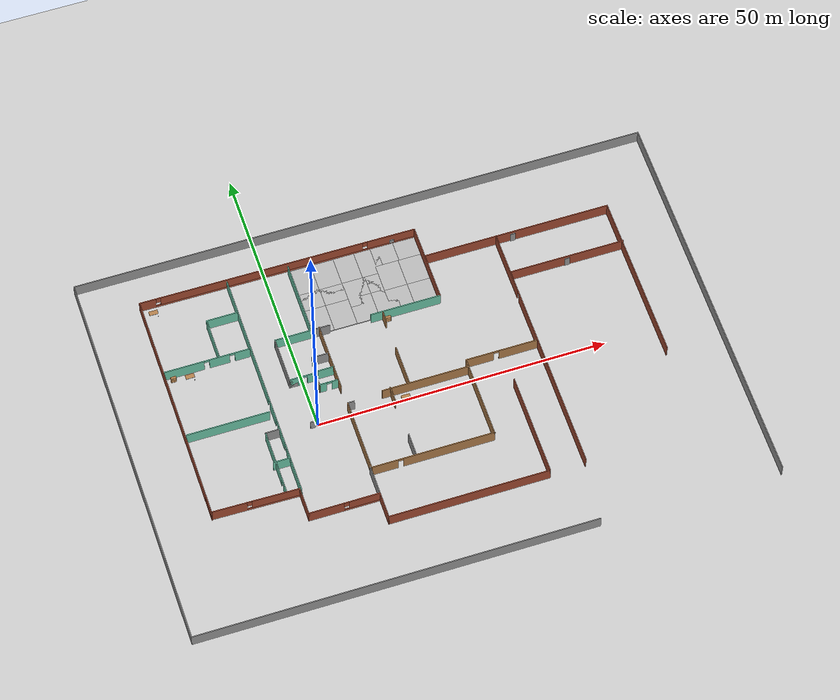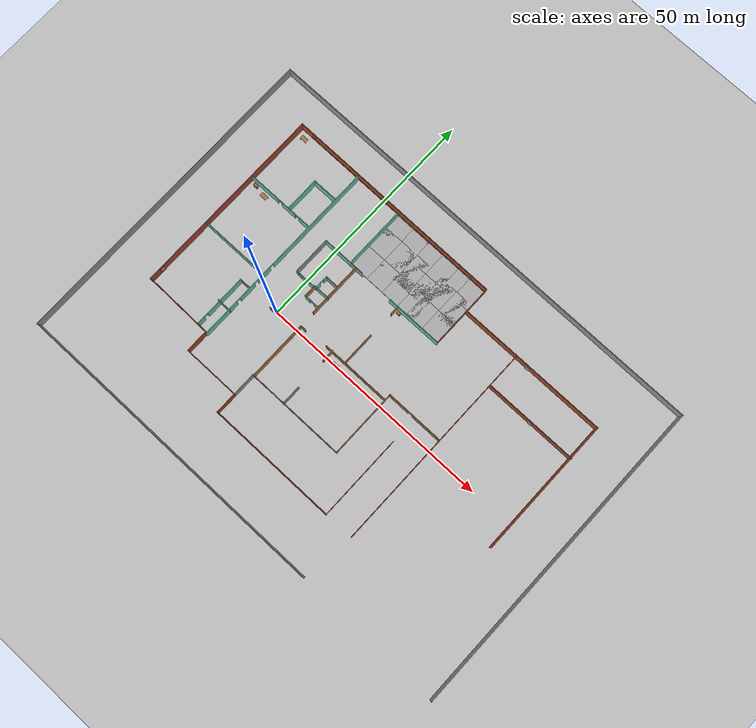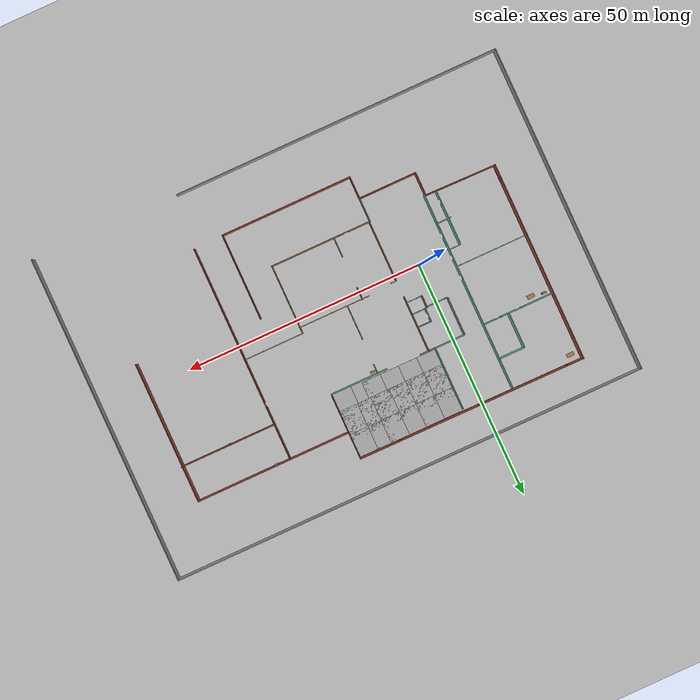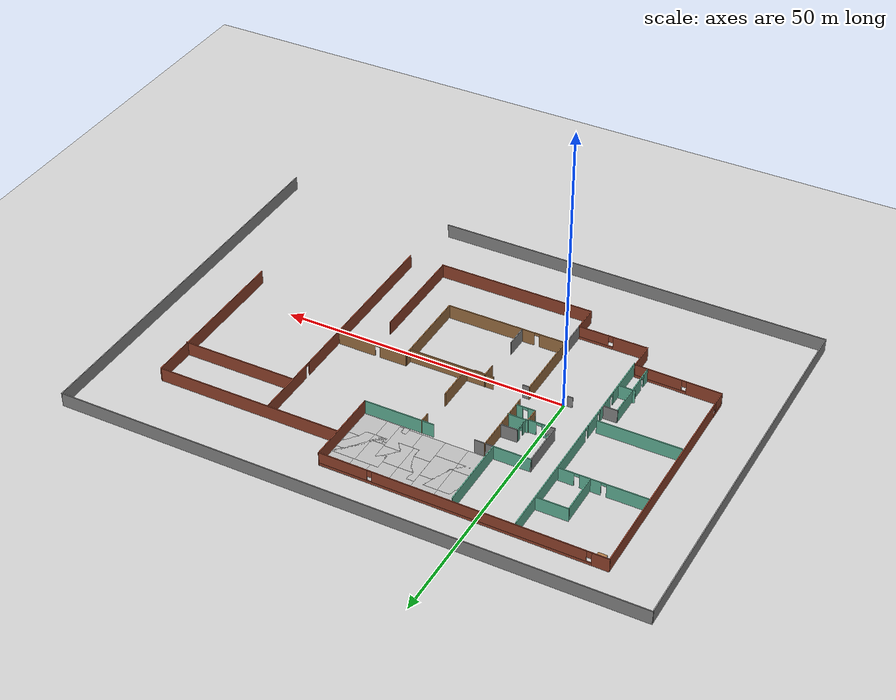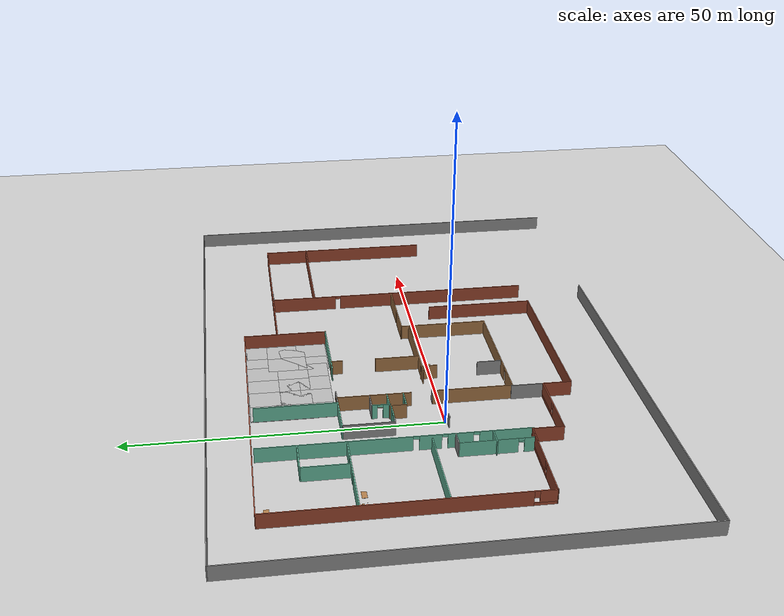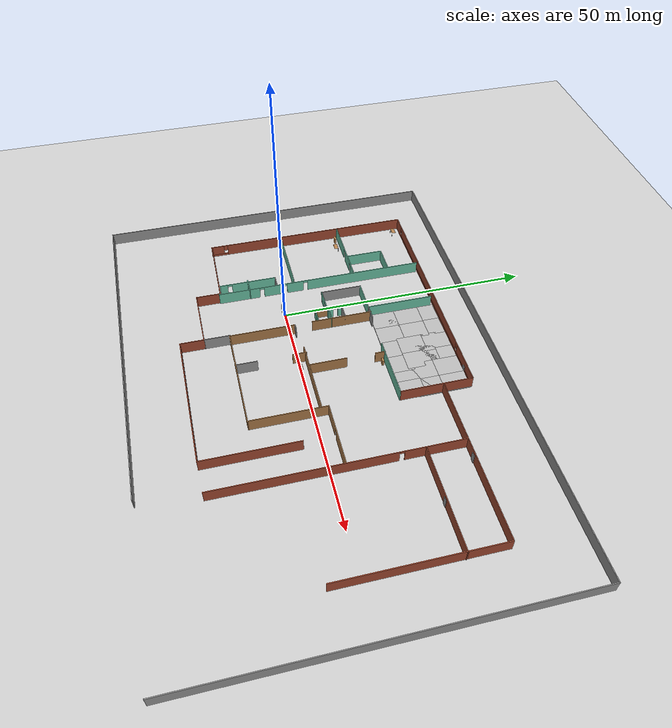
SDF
<sdf version="1.7">
 <world name="empty_world">
  <physics type="ode">
   <max_step_size>0.01</max_step_size>
   <real_time_factor>1</real_time_factor>
   <real_time_update_rate>1000</real_time_update_rate>
  </physics>
  <light name="sun" type="directional">
   <pose>0 0 10 0 -0 0</pose>
   <diffuse>0.8 0.8 0.8 1</diffuse>
   <specular>0.2 0.2 0.2 1</specular>
   <attenuation>
    <range>1000</range>
    <constant>0.9</constant>
    <linear>0.01</linear>
    <quadratic>0.001</quadratic>
   </attenuation>
   <direction>-0.5 0.1 -0.9</direction>
   <spot><inner_angle>0</inner_angle><outer_angle>0</outer_angle><falloff>0</falloff></spot>
  </light>
  <model name="ground_plane">
   <static>1</static>
   <link name="link">
    <collision name="collision">
     <geometry><plane><normal>0 0 1</normal><size>1 1</size></plane></geometry>
    </collision>
    <visual name="visual">
     <geometry><plane><normal>0 0 1</normal><size>100 100</size></plane></geometry>
     <material>
      <ambient>0.8 0.8 0.8 1</ambient>
      <diffuse>0.8 0.8 0.8 1</diffuse>
      <specular>0.8 0.8 0.8 1</specular>
     </material>
    </visual>
   </link>
  </model>
  <gravity>0 0 -9.8</gravity>
  <magnetic_field>6e-06 2.3e-05 -4.2e-05</magnetic_field>
  <atmosphere type="adiabatic"/>
  <scene><ambient>0.4 0.4 0.4 1</ambient><background>0.7 0.7 0.7 1</background><shadows>1</shadows></scene>
  <audio><device>default</device></audio>
  <spherical_coordinates>
   <surface_model>EARTH_WGS84</surface_model>
   <latitude_deg>0</latitude_deg>
   <longitude_deg>0</longitude_deg>
   <elevation>0</elevation>
   <heading_deg>0</heading_deg>
  </spherical_coordinates>
  <model name="house1">
   <pose>18.9218 2.08152 0 0 -0 0</pose>
   <link name="Door_1">
    <collision name="Door_1_Collision">
     <geometry><box><size>0.9 0.17 2</size></box></geometry>
     <pose>0 0 1 0 -0 0</pose>
    </collision>
    <visual name="Door_1_Visual">
     <pose>0 0 1 0 -0 0</pose>
     <geometry><box><size>0.9 0.17 2</size></box></geometry>
     <material>
      <script><uri>file://media/materials/scripts/gazebo.material</uri><name>Gazebo/Grey</name></script>
     </material>
    </visual>
    <pose>30.2713 14.6078 0 0 -0 0</pose>
   </link>
   <link name="Door_2">
    <collision name="Door_2_Collision">
     <geometry><box><size>0.9 0.17 2</size></box></geometry>
     <pose>0 0 1 0 -0 0</pose>
    </collision>
    <visual name="Door_2_Visual">
     <pose>0 0 1 0 -0 0</pose>
     <geometry><box><size>0.9 0.17 2</size></box></geometry>
     <material>
      <script><uri>file://media/materials/scripts/gazebo.material</uri><name>Gazebo/Grey</name></script>
     </material>
    </visual>
    <pose>23.1921 22.0939 0 0 -0 0</pose>
   </link>
   <link name="Door_8">
    <collision name="Door_8_Collision">
     <geometry><box><size>0.9 0.17 2</size></box></geometry>
     <pose>0 0 1 0 -0 0</pose>
    </collision>
    <visual name="Door_8_Visual">
     <pose>0 0 1 0 -0 0</pose>
     <geometry><box><size>0.9 0.17 2</size></box></geometry>
     <material>
      <script><uri>file://media/materials/scripts/gazebo.material</uri><name>Gazebo/Grey</name></script>
     </material>
    </visual>
    <pose>-19.853 -2.39863 0 0 -0 0</pose>
   </link>
   <link name="Wall_0">
    <pose>-40.5454 7.13614 0 0 -0 -1.5708</pose>
    <visual name="Wall_0_Visual_0">
     <pose>-1.72611 0 1.25 0 -0 0</pose>
     <geometry><box><size>38.5478 0.15 2.5</size></box></geometry>
     <material>
      <script><uri>file://media/materials/scripts/gazebo.material</uri><name>Gazebo/Bricks</name></script>
      <ambient>1 1 1 1</ambient>
     </material>
     <meta><layer>0</layer></meta>
    </visual>
    <collision name="Wall_0_Collision_0">
     <geometry><box><size>38.5478 0.15 2.5</size></box></geometry>
     <pose>-1.72611 0 1.25 0 -0 0</pose>
    </collision>
    <visual name="Wall_0_Visual_1">
     <pose>19.2739 0 0.25 0 -0 0</pose>
     <geometry><box><size>3.45222 0.15 0.5</size></box></geometry>
     <material>
      <script><uri>file://media/materials/scripts/gazebo.material</uri><name>Gazebo/Bricks</name></script>
      <ambient>1 1 1 1</ambient>
     </material>
     <meta><layer>0</layer></meta>
    </visual>
    <collision name="Wall_0_Collision_1">
     <geometry><box><size>3.45222 0.15 0.5</size></box></geometry>
     <pose>19.2739 0 0.25 0 -0 0</pose>
    </collision>
    <visual name="Wall_0_Visual_2">
     <pose>19.6739 0 1.5 0 -0 0</pose>
     <geometry><box><size>2.65222 0.15 2</size></box></geometry>
     <material>
      <script><uri>file://media/materials/scripts/gazebo.material</uri><name>Gazebo/Bricks</name></script>
      <ambient>1 1 1 1</ambient>
     </material>
     <meta><layer>0</layer></meta>
    </visual>
    <collision name="Wall_0_Collision_2">
     <geometry><box><size>2.65222 0.15 2</size></box></geometry>
     <pose>19.6739 0 1.5 0 -0 0</pose>
    </collision>
    <visual name="Wall_0_Visual_3">
     <pose>17.9478 0 1.9 0 -0 0</pose>
     <geometry><box><size>0.8 0.15 1.2</size></box></geometry>
     <material>
      <script><uri>file://media/materials/scripts/gazebo.material</uri><name>Gazebo/Bricks</name></script>
      <ambient>1 1 1 1</ambient>
     </material>
     <meta><layer>0</layer></meta>
    </visual>
    <collision name="Wall_0_Collision_3">
     <geometry><box><size>0.8 0.15 1.2</size></box></geometry>
     <pose>17.9478 0 1.9 0 -0 0</pose>
    </collision>
   </link>
   <link name="Wall_1">
    <pose>-33.1204 -13.8596 0 0 -0 -0.019057</pose>
    <visual name="Wall_1_Visual_0">
     <pose>-4.47768 0 1.25 0 -0 0</pose>
     <geometry><box><size>6.04734 0.15 2.5</size></box></geometry>
     <material>
      <script><uri>file://media/materials/scripts/gazebo.material</uri><name>Gazebo/Bricks</name></script>
      <ambient>1 1 1 1</ambient>
     </material>
     <meta><layer>0</layer></meta>
    </visual>
    <collision name="Wall_1_Collision_0">
     <geometry><box><size>6.04734 0.15 2.5</size></box></geometry>
     <pose>-4.47768 0 1.25 0 -0 0</pose>
    </collision>
    <visual name="Wall_1_Visual_1">
     <pose>3.02367 0 0.25 0 -0 0</pose>
     <geometry><box><size>8.95535 0.15 0.5</size></box></geometry>
     <material>
      <script><uri>file://media/materials/scripts/gazebo.material</uri><name>Gazebo/Bricks</name></script>
      <ambient>1 1 1 1</ambient>
     </material>
     <meta><layer>0</layer></meta>
    </visual>
    <collision name="Wall_1_Collision_1">
     <geometry><box><size>8.95535 0.15 0.5</size></box></geometry>
     <pose>3.02367 0 0.25 0 -0 0</pose>
    </collision>
    <visual name="Wall_1_Visual_2">
     <pose>3.42367 0 1.5 0 -0 0</pose>
     <geometry><box><size>8.15535 0.15 2</size></box></geometry>
     <material>
      <script><uri>file://media/materials/scripts/gazebo.material</uri><name>Gazebo/Bricks</name></script>
      <ambient>1 1 1 1</ambient>
     </material>
     <meta><layer>0</layer></meta>
    </visual>
    <collision name="Wall_1_Collision_2">
     <geometry><box><size>8.15535 0.15 2</size></box></geometry>
     <pose>3.42367 0 1.5 0 -0 0</pose>
    </collision>
    <visual name="Wall_1_Visual_3">
     <pose>-1.05401 0 1.9 0 -0 0</pose>
     <geometry><box><size>0.8 0.15 1.2</size></box></geometry>
     <material>
      <script><uri>file://media/materials/scripts/gazebo.material</uri><name>Gazebo/Bricks</name></script>
      <ambient>1 1 1 1</ambient>
     </material>
     <meta><layer>0</layer></meta>
    </visual>
    <collision name="Wall_1_Collision_3">
     <geometry><box><size>0.8 0.15 1.2</size></box></geometry>
     <pose>-1.05401 0 1.9 0 -0 0</pose>
    </collision>
   </link>
   <link name="Wall_10">
    <collision name="Wall_10_Collision">
     <geometry><box><size>12.25 0.15 2.5</size></box></geometry>
     <pose>0 0 1.25 0 -0 0</pose>
    </collision>
    <visual name="Wall_10_Visual">
     <pose>0 0 1.25 0 -0 0</pose>
     <geometry><box><size>12.25 0.15 2.5</size></box></geometry>
     <material>
      <script><uri>file://media/materials/scripts/gazebo.material</uri><name>Gazebo/Grey</name></script>
      <ambient>0.435294 0.796078 0.67451 1</ambient>
     </material>
     <meta><layer>0</layer></meta>
    </visual>
    <pose>1.50463 13.9989 0 0 -0 3.14159</pose>
   </link>
   <link name="Wall_12">
    <collision name="Wall_12_Collision">
     <geometry><box><size>32.5 0.15 2.5</size></box></geometry>
     <pose>0 0 1.25 0 -0 0</pose>
    </collision>
    <visual name="Wall_12_Visual">
     <pose>0 0 1.25 0 -0 0</pose>
     <geometry><box><size>32.5 0.15 2.5</size></box></geometry>
     <material>
      <script><uri>file://media/materials/scripts/gazebo.material</uri><name>Gazebo/Bricks</name></script>
      <ambient>1 1 1 1</ambient>
     </material>
     <meta><layer>0</layer></meta>
    </visual>
    <pose>23.8633 22.2145 0 0 -0 0</pose>
   </link>
   <link name="Wall_13">
    <collision name="Wall_13_Collision">
     <geometry><box><size>29.75 0.15 2.5</size></box></geometry>
     <pose>0 0 1.25 0 -0 0</pose>
    </collision>
    <visual name="Wall_13_Visual">
     <pose>0 0 1.25 0 -0 0</pose>
     <geometry><box><size>29.75 0.15 2.5</size></box></geometry>
     <material>
      <script><uri>file://media/materials/scripts/gazebo.material</uri><name>Gazebo/Bricks</name></script>
      <ambient>1 1 1 1</ambient>
     </material>
     <meta><layer>0</layer></meta>
    </visual>
    <pose>40.0383 7.41453 0 0 -0 -1.5708</pose>
   </link>
   <link name="Wall_16">
    <pose>20.1814 -0.581074 0 0 -0 -1.5708</pose>
    <visual name="Wall_16_Visual_0">
     <pose>-17.1195 0 1.25 0 -0 0</pose>
     <geometry><box><size>11.261 0.15 2.5</size></box></geometry>
     <material>
      <script><uri>file://media/materials/scripts/gazebo.material</uri><name>Gazebo/Bricks</name></script>
      <ambient>1 1 1 1</ambient>
     </material>
     <meta><layer>0</layer></meta>
    </visual>
    <collision name="Wall_16_Collision_0">
     <geometry><box><size>11.261 0.15 2.5</size></box></geometry>
     <pose>-17.1195 0 1.25 0 -0 0</pose>
    </collision>
    <visual name="Wall_16_Visual_1">
     <pose>6.0805 0 1.25 0 -0 0</pose>
     <geometry><box><size>33.339 0.15 2.5</size></box></geometry>
     <material>
      <script><uri>file://media/materials/scripts/gazebo.material</uri><name>Gazebo/Bricks</name></script>
      <ambient>1 1 1 1</ambient>
     </material>
     <meta><layer>0</layer></meta>
    </visual>
    <collision name="Wall_16_Collision_1">
     <geometry><box><size>33.339 0.15 2.5</size></box></geometry>
     <pose>6.0805 0 1.25 0 -0 0</pose>
    </collision>
    <visual name="Wall_16_Visual_2">
     <pose>-11.039 0 2.25 0 -0 0</pose>
     <geometry><box><size>0.9 0.15 0.5</size></box></geometry>
     <material>
      <script><uri>file://media/materials/scripts/gazebo.material</uri><name>Gazebo/Bricks</name></script>
      <ambient>1 1 1 1</ambient>
     </material>
     <meta><layer>0</layer></meta>
    </visual>
    <collision name="Wall_16_Collision_2">
     <geometry><box><size>0.9 0.15 0.5</size></box></geometry>
     <pose>-11.039 0 2.25 0 -0 0</pose>
    </collision>
   </link>
   <link name="Wall_19">
    <pose>13.8436 0.693454 0 0 -0 3.14159</pose>
    <visual name="Wall_19_Visual_0">
     <pose>-2.89297 0 1.25 0 -0 0</pose>
     <geometry><box><size>6.71407 0.15 2.5</size></box></geometry>
     <material>
      <script><uri>file://media/materials/scripts/gazebo.material</uri><name>Gazebo/Wood</name></script>
      <ambient>0.435294 0.796078 0.67451 1</ambient>
     </material>
     <meta><layer>0</layer></meta>
    </visual>
    <collision name="Wall_19_Collision_0">
     <geometry><box><size>6.71407 0.15 2.5</size></box></geometry>
     <pose>-2.89297 0 1.25 0 -0 0</pose>
    </collision>
    <visual name="Wall_19_Visual_1">
     <pose>3.80703 0 1.25 0 -0 0</pose>
     <geometry><box><size>4.88593 0.15 2.5</size></box></geometry>
     <material>
      <script><uri>file://media/materials/scripts/gazebo.material</uri><name>Gazebo/Wood</name></script>
      <ambient>0.435294 0.796078 0.67451 1</ambient>
     </material>
     <meta><layer>0</layer></meta>
    </visual>
    <collision name="Wall_19_Collision_1">
     <geometry><box><size>4.88593 0.15 2.5</size></box></geometry>
     <pose>3.80703 0 1.25 0 -0 0</pose>
    </collision>
    <visual name="Wall_19_Visual_2">
     <pose>0.914068 0 2.25 0 -0 0</pose>
     <geometry><box><size>0.9 0.15 0.5</size></box></geometry>
     <material>
      <script><uri>file://media/materials/scripts/gazebo.material</uri><name>Gazebo/Wood</name></script>
      <ambient>0.435294 0.796078 0.67451 1</ambient>
     </material>
     <meta><layer>0</layer></meta>
    </visual>
    <collision name="Wall_19_Collision_2">
     <geometry><box><size>0.9 0.15 0.5</size></box></geometry>
     <pose>0.914068 0 2.25 0 -0 0</pose>
    </collision>
   </link>
   <link name="Wall_2">
    <collision name="Wall_2_Collision">
     <geometry><box><size>5 0.15 2.5</size></box></geometry>
     <pose>0 0 1.25 0 -0 0</pose>
    </collision>
    <visual name="Wall_2_Visual">
     <pose>0 0 1.25 0 -0 0</pose>
     <geometry><box><size>5 0.15 2.5</size></box></geometry>
     <material>
      <script><uri>file://media/materials/scripts/gazebo.material</uri><name>Gazebo/Bricks</name></script>
      <ambient>1 1 1 1</ambient>
     </material>
     <meta><layer>0</layer></meta>
    </visual>
    <pose>-25.6954 -16.4261 0 0 -0 -1.5708</pose>
   </link>
   <link name="Wall_20">
    <collision name="Wall_20_Collision">
     <geometry><box><size>14.7327 0.15 2.5</size></box></geometry>
     <pose>0 0 1.25 0 -0 0</pose>
    </collision>
    <visual name="Wall_20_Visual">
     <pose>0 0 1.25 0 -0 0</pose>
     <geometry><box><size>14.7327 0.15 2.5</size></box></geometry>
     <material>
      <script><uri>file://media/materials/scripts/gazebo.material</uri><name>Gazebo/Wood</name></script>
      <ambient>0.435294 0.796078 0.67451 1</ambient>
     </material>
     <meta><layer>0</layer></meta>
    </visual>
    <pose>7.66864 -6.59786 0 0 -0 -1.5708</pose>
   </link>
   <link name="Wall_21">
    <pose>-2.83483 -13.8892 0 0 -0 3.14159</pose>
    <visual name="Wall_21_Visual_0">
     <pose>-2.74764 0 1.25 0 -0 0</pose>
     <geometry><box><size>15.7547 0.15 2.5</size></box></geometry>
     <material>
      <script><uri>file://media/materials/scripts/gazebo.material</uri><name>Gazebo/Wood</name></script>
      <ambient>0.435294 0.796078 0.67451 1</ambient>
     </material>
     <meta><layer>0</layer></meta>
    </visual>
    <collision name="Wall_21_Collision_0">
     <geometry><box><size>15.7547 0.15 2.5</size></box></geometry>
     <pose>-2.74764 0 1.25 0 -0 0</pose>
    </collision>
    <visual name="Wall_21_Visual_1">
     <pose>8.32736 0 1.25 0 -0 0</pose>
     <geometry><box><size>4.59528 0.15 2.5</size></box></geometry>
     <material>
      <script><uri>file://media/materials/scripts/gazebo.material</uri><name>Gazebo/Wood</name></script>
      <ambient>0.435294 0.796078 0.67451 1</ambient>
     </material>
     <meta><layer>0</layer></meta>
    </visual>
    <collision name="Wall_21_Collision_1">
     <geometry><box><size>4.59528 0.15 2.5</size></box></geometry>
     <pose>8.32736 0 1.25 0 -0 0</pose>
    </collision>
    <visual name="Wall_21_Visual_2">
     <pose>5.57972 0 2.25 0 -0 0</pose>
     <geometry><box><size>0.9 0.15 0.5</size></box></geometry>
     <material>
      <script><uri>file://media/materials/scripts/gazebo.material</uri><name>Gazebo/Wood</name></script>
      <ambient>0.435294 0.796078 0.67451 1</ambient>
     </material>
     <meta><layer>0</layer></meta>
    </visual>
    <collision name="Wall_21_Collision_2">
     <geometry><box><size>0.9 0.15 0.5</size></box></geometry>
     <pose>5.57972 0 2.25 0 -0 0</pose>
    </collision>
   </link>
   <link name="Wall_22">
    <collision name="Wall_22_Collision">
     <geometry><box><size>12.9827 0.15 2.5</size></box></geometry>
     <pose>0 0 1.25 0 -0 0</pose>
    </collision>
    <visual name="Wall_22_Visual">
     <pose>0 0 1.25 0 -0 0</pose>
     <geometry><box><size>12.9827 0.15 2.5</size></box></geometry>
     <material>
      <script><uri>file://media/materials/scripts/gazebo.material</uri><name>Gazebo/Wood</name></script>
      <ambient>0.435294 0.796078 0.67451 1</ambient>
     </material>
     <meta><layer>0</layer></meta>
    </visual>
    <pose>-13.4314 -7.47286 0 0 -0 1.5708</pose>
   </link>
   <link name="Wall_23">
    <collision name="Wall_23_Collision">
     <geometry><box><size>1.25 0.15 2.5</size></box></geometry>
     <pose>0 0 1.25 0 -0 0</pose>
    </collision>
    <visual name="Wall_23_Visual">
     <pose>0 0 1.25 0 -0 0</pose>
     <geometry><box><size>1.25 0.15 2.5</size></box></geometry>
     <material>
      <script><uri>file://media/materials/scripts/gazebo.material</uri><name>Gazebo/Grey</name></script>
      <ambient>1 1 1 1</ambient>
     </material>
     <meta><layer>0</layer></meta>
    </visual>
    <pose>-12.8814 -1.05655 0 0 -0 0</pose>
   </link>
   <link name="Wall_25">
    <collision name="Wall_25_Collision">
     <geometry><box><size>15 0.15 2.5</size></box></geometry>
     <pose>0 0 1.25 0 -0 0</pose>
    </collision>
    <visual name="Wall_25_Visual">
     <pose>0 0 1.25 0 -0 0</pose>
     <geometry><box><size>15 0.15 2.5</size></box></geometry>
     <material>
      <script><uri>file://media/materials/scripts/gazebo.material</uri><name>Gazebo/Wood</name></script>
      <ambient>0.435294 0.796078 0.67451 1</ambient>
     </material>
     <meta><layer>0</layer></meta>
    </visual>
    <pose>0.143939 -0.608476 0 0 -0 3.14159</pose>
   </link>
   <link name="Wall_27">
    <collision name="Wall_27_Collision">
     <geometry><box><size>7.25 0.15 2.5</size></box></geometry>
     <pose>0 0 1.25 0 -0 0</pose>
    </collision>
    <visual name="Wall_27_Visual">
     <pose>0 0 1.25 0 -0 0</pose>
     <geometry><box><size>7.25 0.15 2.5</size></box></geometry>
     <material>
      <script><uri>file://media/materials/scripts/gazebo.material</uri><name>Gazebo/Wood</name></script>
      <ambient>0.435294 0.796078 0.67451 1</ambient>
     </material>
     <meta><layer>0</layer></meta>
    </visual>
    <pose>-2.60239 3.0229 0 0 -0 1.5708</pose>
   </link>
   <link name="Wall_3">
    <pose>-19.6454 -18.8511 0 0 -0 0</pose>
    <visual name="Wall_3_Visual_0">
     <pose>-3.08149 0 1.25 0 -0 0</pose>
     <geometry><box><size>6.08701 0.15 2.5</size></box></geometry>
     <material>
      <script><uri>file://media/materials/scripts/gazebo.material</uri><name>Gazebo/Bricks</name></script>
      <ambient>1 1 1 1</ambient>
     </material>
     <meta><layer>0</layer></meta>
    </visual>
    <collision name="Wall_3_Collision_0">
     <geometry><box><size>6.08701 0.15 2.5</size></box></geometry>
     <pose>-3.08149 0 1.25 0 -0 0</pose>
    </collision>
    <visual name="Wall_3_Visual_1">
     <pose>3.04351 0 0.25 0 -0 0</pose>
     <geometry><box><size>6.16299 0.15 0.5</size></box></geometry>
     <material>
      <script><uri>file://media/materials/scripts/gazebo.material</uri><name>Gazebo/Bricks</name></script>
      <ambient>1 1 1 1</ambient>
     </material>
     <meta><layer>0</layer></meta>
    </visual>
    <collision name="Wall_3_Collision_1">
     <geometry><box><size>6.16299 0.15 0.5</size></box></geometry>
     <pose>3.04351 0 0.25 0 -0 0</pose>
    </collision>
    <visual name="Wall_3_Visual_2">
     <pose>3.44351 0 1.5 0 -0 0</pose>
     <geometry><box><size>5.36299 0.15 2</size></box></geometry>
     <material>
      <script><uri>file://media/materials/scripts/gazebo.material</uri><name>Gazebo/Bricks</name></script>
      <ambient>1 1 1 1</ambient>
     </material>
     <meta><layer>0</layer></meta>
    </visual>
    <collision name="Wall_3_Collision_2">
     <geometry><box><size>5.36299 0.15 2</size></box></geometry>
     <pose>3.44351 0 1.5 0 -0 0</pose>
    </collision>
    <visual name="Wall_3_Visual_3">
     <pose>0.362009 0 1.9 0 -0 0</pose>
     <geometry><box><size>0.8 0.15 1.2</size></box></geometry>
     <material>
      <script><uri>file://media/materials/scripts/gazebo.material</uri><name>Gazebo/Bricks</name></script>
      <ambient>1 1 1 1</ambient>
     </material>
     <meta><layer>0</layer></meta>
    </visual>
    <collision name="Wall_3_Collision_3">
     <geometry><box><size>0.8 0.15 1.2</size></box></geometry>
     <pose>0.362009 0 1.9 0 -0 0</pose>
    </collision>
   </link>
   <link name="Wall_30">
    <collision name="Wall_30_Collision">
     <geometry><box><size>2 0.15 2.5</size></box></geometry>
     <pose>0 0 1.25 0 -0 0</pose>
    </collision>
    <visual name="Wall_30_Visual">
     <pose>0 0 1.25 0 -0 0</pose>
     <geometry><box><size>2 0.15 2.5</size></box></geometry>
     <material>
      <script><uri>file://media/materials/scripts/gazebo.material</uri><name>Gazebo/Wood</name></script>
      <ambient>0.435294 0.796078 0.67451 1</ambient>
     </material>
     <meta><layer>0</layer></meta>
    </visual>
    <pose>-2.52102 13.1132 0 0 -0 -1.5708</pose>
   </link>
   <link name="Wall_32">
    <collision name="Wall_32_Collision">
     <geometry><box><size>13.25 0.15 2.5</size></box></geometry>
     <pose>0 0 1.25 0 -0 0</pose>
    </collision>
    <visual name="Wall_32_Visual">
     <pose>0 0 1.25 0 -0 0</pose>
     <geometry><box><size>13.25 0.15 2.5</size></box></geometry>
     <material>
      <script><uri>file://media/materials/scripts/gazebo.material</uri><name>Gazebo/Grey</name></script>
      <ambient>0.435294 0.796078 0.67451 1</ambient>
     </material>
     <meta><layer>0</layer></meta>
    </visual>
    <pose>-14.8894 20.7516 0 0 -0 -1.5708</pose>
   </link>
   <link name="Wall_33">
    <collision name="Wall_33_Collision">
     <geometry><box><size>6.5 0.15 2.5</size></box></geometry>
     <pose>0 0 1.25 0 -0 0</pose>
    </collision>
    <visual name="Wall_33_Visual">
     <pose>0 0 1.25 0 -0 0</pose>
     <geometry><box><size>6.5 0.15 2.5</size></box></geometry>
     <material>
      <script><uri>file://media/materials/scripts/gazebo.material</uri><name>Gazebo/Grey</name></script>
      <ambient>0.435294 0.796078 0.67451 1</ambient>
     </material>
     <meta><layer>0</layer></meta>
    </visual>
    <pose>-18.0644 14.2016 0 0 -0 3.14159</pose>
   </link>
   <link name="Wall_34">
    <collision name="Wall_34_Collision">
     <geometry><box><size>8.25 0.15 2.5</size></box></geometry>
     <pose>0 0 1.25 0 -0 0</pose>
    </collision>
    <visual name="Wall_34_Visual">
     <pose>0 0 1.25 0 -0 0</pose>
     <geometry><box><size>8.25 0.15 2.5</size></box></geometry>
     <material>
      <script><uri>file://media/materials/scripts/gazebo.material</uri><name>Gazebo/Grey</name></script>
      <ambient>1 1 1 1</ambient>
     </material>
     <meta><layer>0</layer></meta>
    </visual>
    <pose>-21.2394 10.1516 0 0 -0 -1.5708</pose>
   </link>
   <link name="Wall_35">
    <collision name="Wall_35_Collision">
     <geometry><box><size>1.5 0.15 2.5</size></box></geometry>
     <pose>0 0 1.25 0 -0 0</pose>
    </collision>
    <visual name="Wall_35_Visual">
     <pose>0 0 1.25 0 -0 0</pose>
     <geometry><box><size>1.5 0.15 2.5</size></box></geometry>
     <material>
      <script><uri>file://media/materials/scripts/gazebo.material</uri><name>Gazebo/Grey</name></script>
      <ambient>1 1 1 1</ambient>
     </material>
     <meta><layer>0</layer></meta>
    </visual>
    <pose>-20.5644 6.10165 0 0 -0 0</pose>
   </link>
   <link name="Wall_38">
    <collision name="Wall_38_Collision">
     <geometry><box><size>3.25 0.15 2.5</size></box></geometry>
     <pose>0 0 1.25 0 -0 0</pose>
    </collision>
    <visual name="Wall_38_Visual">
     <pose>0 0 1.25 0 -0 0</pose>
     <geometry><box><size>3.25 0.15 2.5</size></box></geometry>
     <material>
      <script><uri>file://media/materials/scripts/gazebo.material</uri><name>Gazebo/Grey</name></script>
      <ambient>1 1 1 1</ambient>
     </material>
     <meta><layer>0</layer></meta>
    </visual>
    <pose>-13.3394 14.2016 0 0 -0 0</pose>
   </link>
   <link name="Wall_4">
    <collision name="Wall_4_Collision">
     <geometry><box><size>4.75 0.15 2.5</size></box></geometry>
     <pose>0 0 1.25 0 -0 0</pose>
    </collision>
    <visual name="Wall_4_Visual">
     <pose>0 0 1.25 0 -0 0</pose>
     <geometry><box><size>4.75 0.15 2.5</size></box></geometry>
     <material>
      <script><uri>file://media/materials/scripts/gazebo.material</uri><name>Gazebo/Bricks</name></script>
      <ambient>1 1 1 1</ambient>
     </material>
     <meta><layer>0</layer></meta>
    </visual>
    <pose>-13.5954 -21.1511 0 0 -0 -1.5708</pose>
   </link>
   <link name="Wall_40">
    <collision name="Wall_40_Collision">
     <geometry><box><size>12 0.15 2.5</size></box></geometry>
     <pose>0 0 1.25 0 -0 0</pose>
    </collision>
    <visual name="Wall_40_Visual">
     <pose>0 0 1.25 0 -0 0</pose>
     <geometry><box><size>12 0.15 2.5</size></box></geometry>
     <material>
      <script><uri>file://media/materials/scripts/gazebo.material</uri><name>Gazebo/Wood</name></script>
      <ambient>0.435294 0.796078 0.67451 1</ambient>
     </material>
     <meta><layer>0</layer></meta>
    </visual>
    <pose>-13.5061 8.35735 0 0 -0 -1.5708</pose>
   </link>
   <link name="Wall_42">
    <collision name="Wall_42_Collision">
     <geometry><box><size>3 0.15 2.5</size></box></geometry>
     <pose>0 0 1.25 0 -0 0</pose>
    </collision>
    <visual name="Wall_42_Visual">
     <pose>0 0 1.25 0 -0 0</pose>
     <geometry><box><size>3 0.15 2.5</size></box></geometry>
     <material>
      <script><uri>file://media/materials/scripts/gazebo.material</uri><name>Gazebo/Grey</name></script>
      <ambient>1 1 1 1</ambient>
     </material>
     <meta><layer>0</layer></meta>
    </visual>
    <pose>-14.9311 9.07463 0 0 -0 3.14159</pose>
   </link>
   <link name="Wall_43">
    <pose>-16.356 7.64963 0 0 -0 -1.5708</pose>
    <visual name="Wall_43_Visual_0">
     <pose>-1.04184 0 1.25 0 -0 0</pose>
     <geometry><box><size>0.916318 0.15 2.5</size></box></geometry>
     <material>
      <script><uri>file://media/materials/scripts/gazebo.material</uri><name>Gazebo/Grey</name></script>
      <ambient>0.435294 0.796078 0.67451 1</ambient>
     </material>
     <meta><layer>0</layer></meta>
    </visual>
    <collision name="Wall_43_Collision_0">
     <geometry><box><size>0.916318 0.15 2.5</size></box></geometry>
     <pose>-1.04184 0 1.25 0 -0 0</pose>
    </collision>
    <visual name="Wall_43_Visual_1">
     <pose>0.908159 0 1.25 0 -0 0</pose>
     <geometry><box><size>1.18368 0.15 2.5</size></box></geometry>
     <material>
      <script><uri>file://media/materials/scripts/gazebo.material</uri><name>Gazebo/Grey</name></script>
      <ambient>0.435294 0.796078 0.67451 1</ambient>
     </material>
     <meta><layer>0</layer></meta>
    </visual>
    <collision name="Wall_43_Collision_1">
     <geometry><box><size>1.18368 0.15 2.5</size></box></geometry>
     <pose>0.908159 0 1.25 0 -0 0</pose>
    </collision>
    <visual name="Wall_43_Visual_2">
     <pose>-0.133682 0 2.25 0 -0 0</pose>
     <geometry><box><size>0.9 0.15 0.5</size></box></geometry>
     <material>
      <script><uri>file://media/materials/scripts/gazebo.material</uri><name>Gazebo/Grey</name></script>
      <ambient>0.435294 0.796078 0.67451 1</ambient>
     </material>
     <meta><layer>0</layer></meta>
    </visual>
    <collision name="Wall_43_Collision_2">
     <geometry><box><size>0.9 0.15 0.5</size></box></geometry>
     <pose>-0.133682 0 2.25 0 -0 0</pose>
    </collision>
   </link>
   <link name="Wall_45">
    <collision name="Wall_45_Collision">
     <geometry><box><size>3.5 0.15 2.5</size></box></geometry>
     <pose>0 0 1.25 0 -0 0</pose>
    </collision>
    <visual name="Wall_45_Visual">
     <pose>0 0 1.25 0 -0 0</pose>
     <geometry><box><size>3.5 0.15 2.5</size></box></geometry>
     <material>
      <script><uri>file://media/materials/scripts/gazebo.material</uri><name>Gazebo/Grey</name></script>
      <ambient>0.435294 0.796078 0.67451 1</ambient>
     </material>
     <meta><layer>0</layer></meta>
    </visual>
    <pose>-15.0997 6.30803 0 0 -0 3.14159</pose>
   </link>
   <link name="Wall_46">
    <collision name="Wall_46_Collision">
     <geometry><box><size>2.75 0.15 2.5</size></box></geometry>
     <pose>0 0 1.25 0 -0 0</pose>
    </collision>
    <visual name="Wall_46_Visual">
     <pose>0 0 1.25 0 -0 0</pose>
     <geometry><box><size>2.75 0.15 2.5</size></box></geometry>
     <material>
      <script><uri>file://media/materials/scripts/gazebo.material</uri><name>Gazebo/Wood</name></script>
      <ambient>0.435294 0.796078 0.67451 1</ambient>
     </material>
     <meta><layer>0</layer></meta>
    </visual>
    <pose>-16.7747 5.00803 0 0 -0 -1.5708</pose>
   </link>
   <link name="Wall_47">
    <pose>-15.2247 3.70803 0 0 -0 0</pose>
    <visual name="Wall_47_Visual_0">
     <pose>-0.975519 0 1.25 0 -0 0</pose>
     <geometry><box><size>1.29896 0.15 2.5</size></box></geometry>
     <material>
      <script><uri>file://media/materials/scripts/gazebo.material</uri><name>Gazebo/Grey</name></script>
      <ambient>0.435294 0.796078 0.67451 1</ambient>
     </material>
     <meta><layer>0</layer></meta>
    </visual>
    <collision name="Wall_47_Collision_0">
     <geometry><box><size>1.29896 0.15 2.5</size></box></geometry>
     <pose>-0.975519 0 1.25 0 -0 0</pose>
    </collision>
    <visual name="Wall_47_Visual_1">
     <pose>1.09948 0 1.25 0 -0 0</pose>
     <geometry><box><size>1.05104 0.15 2.5</size></box></geometry>
     <material>
      <script><uri>file://media/materials/scripts/gazebo.material</uri><name>Gazebo/Grey</name></script>
      <ambient>0.435294 0.796078 0.67451 1</ambient>
     </material>
     <meta><layer>0</layer></meta>
    </visual>
    <collision name="Wall_47_Collision_1">
     <geometry><box><size>1.05104 0.15 2.5</size></box></geometry>
     <pose>1.09948 0 1.25 0 -0 0</pose>
    </collision>
    <visual name="Wall_47_Visual_2">
     <pose>0.123962 0 2.25 0 -0 0</pose>
     <geometry><box><size>0.9 0.15 0.5</size></box></geometry>
     <material>
      <script><uri>file://media/materials/scripts/gazebo.material</uri><name>Gazebo/Grey</name></script>
      <ambient>0.435294 0.796078 0.67451 1</ambient>
     </material>
     <meta><layer>0</layer></meta>
    </visual>
    <collision name="Wall_47_Collision_2">
     <geometry><box><size>0.9 0.15 0.5</size></box></geometry>
     <pose>0.123962 0 2.25 0 -0 0</pose>
    </collision>
   </link>
   <link name="Wall_49">
    <pose>-25.4675 6.70213 0 0 -0 -1.5708</pose>
    <visual name="Wall_49_Visual_0">
     <pose>-9.18533 0 1.25 0 -0 0</pose>
     <geometry><box><size>23.6293 0.15 2.5</size></box></geometry>
     <material>
      <script><uri>file://media/materials/scripts/gazebo.material</uri><name>Gazebo/Grey</name></script>
      <ambient>0.435294 0.796078 0.67451 1</ambient>
     </material>
     <meta><layer>0</layer></meta>
    </visual>
    <collision name="Wall_49_Collision_0">
     <geometry><box><size>23.6293 0.15 2.5</size></box></geometry>
     <pose>-9.18533 0 1.25 0 -0 0</pose>
    </collision>
    <visual name="Wall_49_Visual_1">
     <pose>5.23565 0 1.25 0 -0 0</pose>
     <geometry><box><size>3.41264 0.15 2.5</size></box></geometry>
     <material>
      <script><uri>file://media/materials/scripts/gazebo.material</uri><name>Gazebo/Grey</name></script>
      <ambient>0.435294 0.796078 0.67451 1</ambient>
     </material>
     <meta><layer>0</layer></meta>
    </visual>
    <collision name="Wall_49_Collision_1">
     <geometry><box><size>3.41264 0.15 2.5</size></box></geometry>
     <pose>5.23565 0 1.25 0 -0 0</pose>
    </collision>
    <visual name="Wall_49_Visual_2">
     <pose>9.79241 0 1.25 0 -0 0</pose>
     <geometry><box><size>3.90087 0.15 2.5</size></box></geometry>
     <material>
      <script><uri>file://media/materials/scripts/gazebo.material</uri><name>Gazebo/Grey</name></script>
      <ambient>0.435294 0.796078 0.67451 1</ambient>
     </material>
     <meta><layer>0</layer></meta>
    </visual>
    <collision name="Wall_49_Collision_2">
     <geometry><box><size>3.90087 0.15 2.5</size></box></geometry>
     <pose>9.79241 0 1.25 0 -0 0</pose>
    </collision>
    <visual name="Wall_49_Visual_3">
     <pose>16.8214 0 1.25 0 -0 0</pose>
     <geometry><box><size>8.35716 0.15 2.5</size></box></geometry>
     <material>
      <script><uri>file://media/materials/scripts/gazebo.material</uri><name>Gazebo/Grey</name></script>
      <ambient>0.435294 0.796078 0.67451 1</ambient>
     </material>
     <meta><layer>0</layer></meta>
    </visual>
    <collision name="Wall_49_Collision_3">
     <geometry><box><size>8.35716 0.15 2.5</size></box></geometry>
     <pose>16.8214 0 1.25 0 -0 0</pose>
    </collision>
    <visual name="Wall_49_Visual_4">
     <pose>3.07933 0 2.25 0 -0 0</pose>
     <geometry><box><size>0.9 0.15 0.5</size></box></geometry>
     <material>
      <script><uri>file://media/materials/scripts/gazebo.material</uri><name>Gazebo/Grey</name></script>
      <ambient>0.435294 0.796078 0.67451 1</ambient>
     </material>
     <meta><layer>0</layer></meta>
    </visual>
    <collision name="Wall_49_Collision_4">
     <geometry><box><size>0.9 0.15 0.5</size></box></geometry>
     <pose>3.07933 0 2.25 0 -0 0</pose>
    </collision>
    <visual name="Wall_49_Visual_5">
     <pose>7.39197 0 2.25 0 -0 0</pose>
     <geometry><box><size>0.9 0.15 0.5</size></box></geometry>
     <material>
      <script><uri>file://media/materials/scripts/gazebo.material</uri><name>Gazebo/Grey</name></script>
      <ambient>0.435294 0.796078 0.67451 1</ambient>
     </material>
     <meta><layer>0</layer></meta>
    </visual>
    <collision name="Wall_49_Collision_5">
     <geometry><box><size>0.9 0.15 0.5</size></box></geometry>
     <pose>7.39197 0 2.25 0 -0 0</pose>
    </collision>
    <visual name="Wall_49_Visual_6">
     <pose>12.1928 0 2.25 0 -0 0</pose>
     <geometry><box><size>0.9 0.15 0.5</size></box></geometry>
     <material>
      <script><uri>file://media/materials/scripts/gazebo.material</uri><name>Gazebo/Grey</name></script>
      <ambient>0.435294 0.796078 0.67451 1</ambient>
     </material>
     <meta><layer>0</layer></meta>
    </visual>
    <collision name="Wall_49_Collision_6">
     <geometry><box><size>0.9 0.15 0.5</size></box></geometry>
     <pose>12.1928 0 2.25 0 -0 0</pose>
    </collision>
   </link>
   <link name="Wall_5">
    <collision name="Wall_5_Collision">
     <geometry><box><size>27.75 0.15 2.5</size></box></geometry>
     <pose>0 0 1.25 0 -0 0</pose>
    </collision>
    <visual name="Wall_5_Visual">
     <pose>0 0 1.25 0 -0 0</pose>
     <geometry><box><size>27.75 0.15 2.5</size></box></geometry>
     <material>
      <script><uri>file://media/materials/scripts/gazebo.material</uri><name>Gazebo/Bricks</name></script>
      <ambient>1 1 1 1</ambient>
     </material>
     <meta><layer>0</layer></meta>
    </visual>
    <pose>0.204628 -23.4511 0 0 -0 0</pose>
   </link>
   <link name="Wall_51">
    <collision name="Wall_51_Collision">
     <geometry><box><size>2.5 0.15 2.5</size></box></geometry>
     <pose>0 0 1.25 0 -0 0</pose>
    </collision>
    <visual name="Wall_51_Visual">
     <pose>0 0 1.25 0 -0 0</pose>
     <geometry><box><size>2.5 0.15 2.5</size></box></geometry>
     <material>
      <script><uri>file://media/materials/scripts/gazebo.material</uri><name>Gazebo/Grey</name></script>
      <ambient>1 1 1 1</ambient>
     </material>
     <meta><layer>0</layer></meta>
    </visual>
    <pose>-26.7239 -2.31726 0 0 -0 3.14159</pose>
   </link>
   <link name="Wall_52">
    <pose>-27.8989 -7.99226 0 0 -0 -1.5708</pose>
    <visual name="Wall_52_Visual_0">
     <pose>-1.218 0 1.25 0 -0 0</pose>
     <geometry><box><size>9.06399 0.15 2.5</size></box></geometry>
     <material>
      <script><uri>file://media/materials/scripts/gazebo.material</uri><name>Gazebo/Grey</name></script>
      <ambient>0.435294 0.796078 0.67451 1</ambient>
     </material>
     <meta><layer>0</layer></meta>
    </visual>
    <collision name="Wall_52_Collision_0">
     <geometry><box><size>9.06399 0.15 2.5</size></box></geometry>
     <pose>-1.218 0 1.25 0 -0 0</pose>
    </collision>
    <visual name="Wall_52_Visual_1">
     <pose>4.982 0 1.25 0 -0 0</pose>
     <geometry><box><size>1.53601 0.15 2.5</size></box></geometry>
     <material>
      <script><uri>file://media/materials/scripts/gazebo.material</uri><name>Gazebo/Grey</name></script>
      <ambient>0.435294 0.796078 0.67451 1</ambient>
     </material>
     <meta><layer>0</layer></meta>
    </visual>
    <collision name="Wall_52_Collision_1">
     <geometry><box><size>1.53601 0.15 2.5</size></box></geometry>
     <pose>4.982 0 1.25 0 -0 0</pose>
    </collision>
    <visual name="Wall_52_Visual_2">
     <pose>3.76399 0 2.25 0 -0 0</pose>
     <geometry><box><size>0.9 0.15 0.5</size></box></geometry>
     <material>
      <script><uri>file://media/materials/scripts/gazebo.material</uri><name>Gazebo/Grey</name></script>
      <ambient>0.435294 0.796078 0.67451 1</ambient>
     </material>
     <meta><layer>0</layer></meta>
    </visual>
    <collision name="Wall_52_Collision_2">
     <geometry><box><size>0.9 0.15 0.5</size></box></geometry>
     <pose>3.76399 0 2.25 0 -0 0</pose>
    </collision>
   </link>
   <link name="Wall_54">
    <collision name="Wall_54_Collision">
     <geometry><box><size>3 0.15 2.5</size></box></geometry>
     <pose>0 0 1.25 0 -0 0</pose>
    </collision>
    <visual name="Wall_54_Visual">
     <pose>0 0 1.25 0 -0 0</pose>
     <geometry><box><size>3 0.15 2.5</size></box></geometry>
     <material>
      <script><uri>file://media/materials/scripts/gazebo.material</uri><name>Gazebo/Grey</name></script>
      <ambient>0.435294 0.796078 0.67451 1</ambient>
     </material>
     <meta><layer>0</layer></meta>
    </visual>
    <pose>-26.8905 -8.0132 0 0 -0 0</pose>
   </link>
   <link name="Wall_56">
    <collision name="Wall_56_Collision">
     <geometry><box><size>14.25 0.15 2.5</size></box></geometry>
     <pose>0 0 1.25 0 -0 0</pose>
    </collision>
    <visual name="Wall_56_Visual">
     <pose>0 0 1.25 0 -0 0</pose>
     <geometry><box><size>14.25 0.15 2.5</size></box></geometry>
     <material>
      <script><uri>file://media/materials/scripts/gazebo.material</uri><name>Gazebo/Grey</name></script>
      <ambient>0.435294 0.796078 0.67451 1</ambient>
     </material>
     <meta><layer>0</layer></meta>
    </visual>
    <pose>-33.227 1.34442 0 0 -0 0</pose>
   </link>
   <link name="Wall_58">
    <pose>-33.0584 13.9569 0 0 -0 0</pose>
    <visual name="Wall_58_Visual_0">
     <pose>-3.94151 0 1.25 0 -0 0</pose>
     <geometry><box><size>6.86699 0.15 2.5</size></box></geometry>
     <material>
      <script><uri>file://media/materials/scripts/gazebo.material</uri><name>Gazebo/Grey</name></script>
      <ambient>0.435294 0.796078 0.67451 1</ambient>
     </material>
     <meta><layer>0</layer></meta>
    </visual>
    <collision name="Wall_58_Collision_0">
     <geometry><box><size>6.86699 0.15 2.5</size></box></geometry>
     <pose>-3.94151 0 1.25 0 -0 0</pose>
    </collision>
    <visual name="Wall_58_Visual_1">
     <pose>2.13899 0 1.25 0 -0 0</pose>
     <geometry><box><size>3.49401 0.15 2.5</size></box></geometry>
     <material>
      <script><uri>file://media/materials/scripts/gazebo.material</uri><name>Gazebo/Grey</name></script>
      <ambient>0.435294 0.796078 0.67451 1</ambient>
     </material>
     <meta><layer>0</layer></meta>
    </visual>
    <collision name="Wall_58_Collision_1">
     <geometry><box><size>3.49401 0.15 2.5</size></box></geometry>
     <pose>2.13899 0 1.25 0 -0 0</pose>
    </collision>
    <visual name="Wall_58_Visual_2">
     <pose>6.0805 0 1.25 0 -0 0</pose>
     <geometry><box><size>2.589 0.15 2.5</size></box></geometry>
     <material>
      <script><uri>file://media/materials/scripts/gazebo.material</uri><name>Gazebo/Grey</name></script>
      <ambient>0.435294 0.796078 0.67451 1</ambient>
     </material>
     <meta><layer>0</layer></meta>
    </visual>
    <collision name="Wall_58_Collision_2">
     <geometry><box><size>2.589 0.15 2.5</size></box></geometry>
     <pose>6.0805 0 1.25 0 -0 0</pose>
    </collision>
    <visual name="Wall_58_Visual_3">
     <pose>-0.058014 0 2.25 0 -0 0</pose>
     <geometry><box><size>0.9 0.15 0.5</size></box></geometry>
     <material>
      <script><uri>file://media/materials/scripts/gazebo.material</uri><name>Gazebo/Grey</name></script>
      <ambient>0.435294 0.796078 0.67451 1</ambient>
     </material>
     <meta><layer>0</layer></meta>
    </visual>
    <collision name="Wall_58_Collision_3">
     <geometry><box><size>0.9 0.15 0.5</size></box></geometry>
     <pose>-0.058014 0 2.25 0 -0 0</pose>
    </collision>
    <visual name="Wall_58_Visual_4">
     <pose>4.336 0 2.25 0 -0 0</pose>
     <geometry><box><size>0.9 0.15 0.5</size></box></geometry>
     <material>
      <script><uri>file://media/materials/scripts/gazebo.material</uri><name>Gazebo/Grey</name></script>
      <ambient>0.435294 0.796078 0.67451 1</ambient>
     </material>
     <meta><layer>0</layer></meta>
    </visual>
    <collision name="Wall_58_Collision_4">
     <geometry><box><size>0.9 0.15 0.5</size></box></geometry>
     <pose>4.336 0 2.25 0 -0 0</pose>
    </collision>
   </link>
   <link name="Wall_6">
    <collision name="Wall_6_Collision">
     <geometry><box><size>18.25 0.15 2.5</size></box></geometry>
     <pose>0 0 1.25 0 -0 0</pose>
    </collision>
    <visual name="Wall_6_Visual">
     <pose>0 0 1.25 0 -0 0</pose>
     <geometry><box><size>18.25 0.15 2.5</size></box></geometry>
     <material>
      <script><uri>file://media/materials/scripts/gazebo.material</uri><name>Gazebo/Bricks</name></script>
      <ambient>1 1 1 1</ambient>
     </material>
     <meta><layer>0</layer></meta>
    </visual>
    <pose>14.0046 -14.4011 0 0 -0 1.5708</pose>
   </link>
   <link name="Wall_60">
    <collision name="Wall_60_Collision">
     <geometry><box><size>5.5 0.15 2.5</size></box></geometry>
     <pose>0 0 1.25 0 -0 0</pose>
    </collision>
    <visual name="Wall_60_Visual">
     <pose>0 0 1.25 0 -0 0</pose>
     <geometry><box><size>5.5 0.15 2.5</size></box></geometry>
     <material>
      <script><uri>file://media/materials/scripts/gazebo.material</uri><name>Gazebo/Grey</name></script>
      <ambient>0.435294 0.796078 0.67451 1</ambient>
     </material>
     <meta><layer>0</layer></meta>
    </visual>
    <pose>-28.2239 21.3616 0 0 -0 3.14159</pose>
   </link>
   <link name="Wall_61">
    <collision name="Wall_61_Collision">
     <geometry><box><size>7.5 0.15 2.5</size></box></geometry>
     <pose>0 0 1.25 0 -0 0</pose>
    </collision>
    <visual name="Wall_61_Visual">
     <pose>0 0 1.25 0 -0 0</pose>
     <geometry><box><size>7.5 0.15 2.5</size></box></geometry>
     <material>
      <script><uri>file://media/materials/scripts/gazebo.material</uri><name>Gazebo/Grey</name></script>
      <ambient>0.435294 0.796078 0.67451 1</ambient>
     </material>
     <meta><layer>0</layer></meta>
    </visual>
    <pose>-30.8989 17.6866 0 0 -0 -1.5708</pose>
   </link>
   <link name="Wall_63">
    <collision name="Wall_63_Collision">
     <geometry><box><size>20 0.15 2.5</size></box></geometry>
     <pose>0 0 1.25 0 -0 0</pose>
    </collision>
    <visual name="Wall_63_Visual">
     <pose>0 0 1.25 0 -0 0</pose>
     <geometry><box><size>20 0.15 2.5</size></box></geometry>
     <material>
      <script><uri>file://media/materials/scripts/gazebo.material</uri><name>Gazebo/Bricks</name></script>
      <ambient>1 1 1 1</ambient>
     </material>
     <meta><layer>0</layer></meta>
    </visual>
    <pose>30.2691 14.6892 0 0 -0 0</pose>
   </link>
   <link name="Wall_65">
    <collision name="Wall_65_Collision">
     <geometry><box><size>4 0.15 2.5</size></box></geometry>
     <pose>0 0 1.25 0 -0 0</pose>
    </collision>
    <visual name="Wall_65_Visual">
     <pose>0 0 1.25 0 -0 0</pose>
     <geometry><box><size>4 0.15 2.5</size></box></geometry>
     <material>
      <script><uri>file://media/materials/scripts/gazebo.material</uri><name>Gazebo/Grey</name></script>
      <ambient>1 1 1 1</ambient>
     </material>
     <meta><layer>0</layer></meta>
    </visual>
    <pose>-5.77584 -11.7841 0 0 -0 1.5708</pose>
   </link>
   <link name="Wall_67">
    <collision name="Wall_67_Collision">
     <geometry><box><size>2.75 0.15 2.5</size></box></geometry>
     <pose>0 0 1.25 0 -0 0</pose>
    </collision>
    <visual name="Wall_67_Visual">
     <pose>0 0 1.25 0 -0 0</pose>
     <geometry><box><size>2.75 0.15 2.5</size></box></geometry>
     <material>
      <script><uri>file://media/materials/scripts/gazebo.material</uri><name>Gazebo/Wood</name></script>
      <ambient>0.435294 0.796078 0.67451 1</ambient>
     </material>
     <meta><layer>0</layer></meta>
    </visual>
    <pose>-5.85721 -1.74573 0 0 -0 -1.5708</pose>
   </link>
   <link name="Wall_69">
    <collision name="Wall_69_Collision">
     <geometry><box><size>5.25 0.15 2.5</size></box></geometry>
     <pose>0 0 1.25 0 -0 0</pose>
    </collision>
    <visual name="Wall_69_Visual">
     <pose>0 0 1.25 0 -0 0</pose>
     <geometry><box><size>5.25 0.15 2.5</size></box></geometry>
     <material>
      <script><uri>file://media/materials/scripts/gazebo.material</uri><name>Gazebo/Grey</name></script>
      <ambient>1 1 1 1</ambient>
     </material>
     <meta><layer>0</layer></meta>
    </visual>
    <pose>-13.5954 -16.3011 0 0 -0 1.5708</pose>
   </link>
   <link name="Wall_74">
    <collision name="Wall_74_Collision">
     <geometry><box><size>8.25 0.15 2.5</size></box></geometry>
     <pose>0 0 1.25 0 -0 0</pose>
    </collision>
    <visual name="Wall_74_Visual">
     <pose>0 0 1.25 0 -0 0</pose>
     <geometry><box><size>8.25 0.15 2.5</size></box></geometry>
     <material>
      <script><uri>file://media/materials/scripts/gazebo.material</uri><name>Gazebo/Grey</name></script>
      <ambient>0.435294 0.796078 0.67451 1</ambient>
     </material>
     <meta><layer>0</layer></meta>
    </visual>
    <pose>-21.2394 10.1516 0 0 -0 -1.5708</pose>
   </link>
   <link name="Wall_76">
    <pose>-19.0644 6.10165 0 0 -0 0</pose>
    <visual name="Wall_76_Visual_0">
     <pose>-1.12816 0 1.25 0 -0 0</pose>
     <geometry><box><size>2.24369 0.15 2.5</size></box></geometry>
     <material>
      <script><uri>file://media/materials/scripts/gazebo.material</uri><name>Gazebo/Grey</name></script>
      <ambient>0.435294 0.796078 0.67451 1</ambient>
     </material>
     <meta><layer>0</layer></meta>
    </visual>
    <collision name="Wall_76_Collision_0">
     <geometry><box><size>2.24369 0.15 2.5</size></box></geometry>
     <pose>-1.12816 0 1.25 0 -0 0</pose>
    </collision>
    <visual name="Wall_76_Visual_1">
     <pose>1.57184 0 1.25 0 -0 0</pose>
     <geometry><box><size>1.35631 0.15 2.5</size></box></geometry>
     <material>
      <script><uri>file://media/materials/scripts/gazebo.material</uri><name>Gazebo/Grey</name></script>
      <ambient>0.435294 0.796078 0.67451 1</ambient>
     </material>
     <meta><layer>0</layer></meta>
    </visual>
    <collision name="Wall_76_Collision_1">
     <geometry><box><size>1.35631 0.15 2.5</size></box></geometry>
     <pose>1.57184 0 1.25 0 -0 0</pose>
    </collision>
    <visual name="Wall_76_Visual_2">
     <pose>0.443689 0 2.25 0 -0 0</pose>
     <geometry><box><size>0.9 0.15 0.5</size></box></geometry>
     <material>
      <script><uri>file://media/materials/scripts/gazebo.material</uri><name>Gazebo/Grey</name></script>
      <ambient>0.435294 0.796078 0.67451 1</ambient>
     </material>
     <meta><layer>0</layer></meta>
    </visual>
    <collision name="Wall_76_Collision_2">
     <geometry><box><size>0.9 0.15 0.5</size></box></geometry>
     <pose>0.443689 0 2.25 0 -0 0</pose>
    </collision>
   </link>
   <link name="Wall_78">
    <collision name="Wall_78_Collision">
     <geometry><box><size>69.25 0.15 2.5</size></box></geometry>
     <pose>0 0 1.25 0 -0 0</pose>
    </collision>
    <visual name="Wall_78_Visual">
     <pose>0 0 1.25 0 -0 0</pose>
     <geometry><box><size>69.25 0.15 2.5</size></box></geometry>
     <material>
      <script><uri>file://media/materials/scripts/gazebo.material</uri><name>Gazebo/Grey</name></script>
      <ambient>1 1 1 1</ambient>
     </material>
     <meta><layer>0</layer></meta>
    </visual>
    <pose>-50.05 0.125 0 0 -0 -1.5708</pose>
   </link>
   <link name="Wall_79">
    <collision name="Wall_79_Collision">
     <geometry><box><size>69 0.15 2.5</size></box></geometry>
     <pose>0 0 1.25 0 -0 0</pose>
    </collision>
    <visual name="Wall_79_Visual">
     <pose>0 0 1.25 0 -0 0</pose>
     <geometry><box><size>69 0.15 2.5</size></box></geometry>
     <material>
      <script><uri>file://media/materials/scripts/gazebo.material</uri><name>Gazebo/Grey</name></script>
      <ambient>0 0 0 1</ambient>
     </material>
     <meta><layer>0</layer></meta>
    </visual>
    <pose>-15.625 -34.425 0 0 -0 0</pose>
   </link>
   <link name="Wall_8">
    <pose>-16.4954 27.9904 0 0 -0 -0.005884</pose>
    <visual name="Wall_8_Visual_0">
     <pose>-22.6888 0 1.25 0 -0 0</pose>
     <geometry><box><size>2.87237 0.15 2.5</size></box></geometry>
     <material>
      <script><uri>file://media/materials/scripts/gazebo.material</uri><name>Gazebo/Bricks</name></script>
      <ambient>1 1 1 1</ambient>
     </material>
     <meta><layer>0</layer></meta>
    </visual>
    <collision name="Wall_8_Collision_0">
     <geometry><box><size>2.87237 0.15 2.5</size></box></geometry>
     <pose>-22.6888 0 1.25 0 -0 0</pose>
    </collision>
    <visual name="Wall_8_Visual_1">
     <pose>1.43619 0 0.25 0 -0 0</pose>
     <geometry><box><size>45.3776 0.15 0.5</size></box></geometry>
     <material>
      <script><uri>file://media/materials/scripts/gazebo.material</uri><name>Gazebo/Bricks</name></script>
      <ambient>1 1 1 1</ambient>
     </material>
     <meta><layer>0</layer></meta>
    </visual>
    <collision name="Wall_8_Collision_1">
     <geometry><box><size>45.3776 0.15 0.5</size></box></geometry>
     <pose>1.43619 0 0.25 0 -0 0</pose>
    </collision>
    <visual name="Wall_8_Visual_2">
     <pose>-2.78544 0 1.5 0 -0 0</pose>
     <geometry><box><size>35.3344 0.15 2</size></box></geometry>
     <material>
      <script><uri>file://media/materials/scripts/gazebo.material</uri><name>Gazebo/Bricks</name></script>
      <ambient>1 1 1 1</ambient>
     </material>
     <meta><layer>0</layer></meta>
    </visual>
    <collision name="Wall_8_Collision_2">
     <geometry><box><size>35.3344 0.15 2</size></box></geometry>
     <pose>-2.78544 0 1.5 0 -0 0</pose>
    </collision>
    <visual name="Wall_8_Visual_3">
     <pose>19.9034 0 1.5 0 -0 0</pose>
     <geometry><box><size>8.44325 0.15 2</size></box></geometry>
     <material>
      <script><uri>file://media/materials/scripts/gazebo.material</uri><name>Gazebo/Bricks</name></script>
      <ambient>1 1 1 1</ambient>
     </material>
     <meta><layer>0</layer></meta>
    </visual>
    <collision name="Wall_8_Collision_3">
     <geometry><box><size>8.44325 0.15 2</size></box></geometry>
     <pose>19.9034 0 1.5 0 -0 0</pose>
    </collision>
    <visual name="Wall_8_Visual_4">
     <pose>-20.8526 0 1.9 0 -0 0</pose>
     <geometry><box><size>0.8 0.15 1.2</size></box></geometry>
     <material>
      <script><uri>file://media/materials/scripts/gazebo.material</uri><name>Gazebo/Bricks</name></script>
      <ambient>1 1 1 1</ambient>
     </material>
     <meta><layer>0</layer></meta>
    </visual>
    <collision name="Wall_8_Collision_4">
     <geometry><box><size>0.8 0.15 1.2</size></box></geometry>
     <pose>-20.8526 0 1.9 0 -0 0</pose>
    </collision>
    <visual name="Wall_8_Visual_5">
     <pose>15.2817 0 1.9 0 -0 0</pose>
     <geometry><box><size>0.8 0.15 1.2</size></box></geometry>
     <material>
      <script><uri>file://media/materials/scripts/gazebo.material</uri><name>Gazebo/Bricks</name></script>
      <ambient>1 1 1 1</ambient>
     </material>
     <meta><layer>0</layer></meta>
    </visual>
    <collision name="Wall_8_Collision_5">
     <geometry><box><size>0.8 0.15 1.2</size></box></geometry>
     <pose>15.2817 0 1.9 0 -0 0</pose>
    </collision>
   </link>
   <link name="Wall_84">
    <collision name="Wall_84_Collision">
     <geometry><box><size>100.25 0.15 2.5</size></box></geometry>
     <pose>0 0 1.25 0 -0 0</pose>
    </collision>
    <visual name="Wall_84_Visual">
     <pose>0 0 1.25 0 -0 0</pose>
     <geometry><box><size>100.25 0.15 2.5</size></box></geometry>
     <material>
      <script><uri>file://media/materials/scripts/gazebo.material</uri><name>Gazebo/Grey</name></script>
      <ambient>0 0 0 1</ambient>
     </material>
     <meta><layer>0</layer></meta>
    </visual>
    <pose>1e-06 34.675 0 0 -0 0</pose>
   </link>
   <link name="Wall_85">
    <collision name="Wall_85_Collision">
     <geometry><box><size>69.5 0.15 2.5</size></box></geometry>
     <pose>0 0 1.25 0 -0 0</pose>
    </collision>
    <visual name="Wall_85_Visual">
     <pose>0 0 1.25 0 -0 0</pose>
     <geometry><box><size>69.5 0.15 2.5</size></box></geometry>
     <material>
      <script><uri>file://media/materials/scripts/gazebo.material</uri><name>Gazebo/Grey</name></script>
      <ambient>0 0 0 1</ambient>
     </material>
     <meta><layer>0</layer></meta>
    </visual>
    <pose>50.05 -0 0 0 -0 -1.5708</pose>
   </link>
   <link name="Wall_9">
    <collision name="Wall_9_Collision">
     <geometry><box><size>14 0.15 2.5</size></box></geometry>
     <pose>0 0 1.25 0 -0 0</pose>
    </collision>
    <visual name="Wall_9_Visual">
     <pose>0 0 1.25 0 -0 0</pose>
     <geometry><box><size>14 0.15 2.5</size></box></geometry>
     <material>
      <script><uri>file://media/materials/scripts/gazebo.material</uri><name>Gazebo/Bricks</name></script>
      <ambient>1 1 1 1</ambient>
     </material>
     <meta><layer>0</layer></meta>
    </visual>
    <pose>7.55463 20.9239 0 0 -0 -1.5708</pose>
   </link>
   <link name="Window_6">
    <collision name="Window_6_Collision">
     <geometry><box><size>0.8 0.17 0.8</size></box></geometry>
     <pose>0 0 0.4 0 -0 0</pose>
    </collision>
    <visual name="Window_6_Visual">
     <pose>0 0 0.4 0 -0 0</pose>
     <geometry><box><size>0.8 0.17 0.8</size></box></geometry>
     <material>
      <script><uri>file://media/materials/scripts/gazebo.material</uri><name>Gazebo/Grey</name></script>
     </material>
    </visual>
    <pose>3.52704 27.7225 0.5 0 -0 0</pose>
   </link>
   <static>1</static>
  </model>
  <model name="table">
   <static>1</static>
   <link name="link">
    <collision name="surface">
     <pose>0 0 1 0 -0 0</pose>
     <geometry><box><size>1.5 0.8 0.03</size></box></geometry>
     <surface><friction><ode><mu>0.6</mu><mu2>0.6</mu2></ode></friction></surface>
    </collision>
    <visual name="visual1">
     <pose>0 0 1 0 -0 0</pose>
     <geometry><box><size>1.5 0.8 0.03</size></box></geometry>
     <material>
      <script><uri>file://media/materials/scripts/gazebo.material</uri><name>Gazebo/Wood</name></script>
     </material>
    </visual>
    <collision name="front_left_leg">
     <pose>0.68 0.38 0.5 0 -0 0</pose>
     <geometry><cylinder><radius>0.02</radius><length>1</length></cylinder></geometry>
    </collision>
    <visual name="front_left_leg">
     <pose>0.68 0.38 0.5 0 -0 0</pose>
     <geometry><cylinder><radius>0.02</radius><length>1</length></cylinder></geometry>
     <material>
      <script><uri>file://media/materials/scripts/gazebo.material</uri><name>Gazebo/Grey</name></script>
     </material>
    </visual>
    <collision name="front_right_leg">
     <pose>0.68 -0.38 0.5 0 -0 0</pose>
     <geometry><cylinder><radius>0.02</radius><length>1</length></cylinder></geometry>
    </collision>
    <visual name="front_right_leg">
     <pose>0.68 -0.38 0.5 0 -0 0</pose>
     <geometry><cylinder><radius>0.02</radius><length>1</length></cylinder></geometry>
     <material>
      <script><uri>file://media/materials/scripts/gazebo.material</uri><name>Gazebo/Grey</name></script>
     </material>
    </visual>
    <collision name="back_right_leg">
     <pose>-0.68 -0.38 0.5 0 -0 0</pose>
     <geometry><cylinder><radius>0.02</radius><length>1</length></cylinder></geometry>
    </collision>
    <visual name="back_right_leg">
     <pose>-0.68 -0.38 0.5 0 -0 0</pose>
     <geometry><cylinder><radius>0.02</radius><length>1</length></cylinder></geometry>
     <material>
      <script><uri>file://media/materials/scripts/gazebo.material</uri><name>Gazebo/Grey</name></script>
     </material>
    </visual>
    <collision name="back_left_leg">
     <pose>-0.68 0.38 0.5 0 -0 0</pose>
     <geometry><cylinder><radius>0.02</radius><length>1</length></cylinder></geometry>
    </collision>
    <visual name="back_left_leg">
     <pose>-0.68 0.38 0.5 0 -0 0</pose>
     <geometry><cylinder><radius>0.02</radius><length>1</length></cylinder></geometry>
     <material>
      <script><uri>file://media/materials/scripts/gazebo.material</uri><name>Gazebo/Grey</name></script>
     </material>
    </visual>
   </link>
   <pose>-19.7579 28.6277 0 0 -0 0</pose>
  </model>
  <model name="table_0">
   <static>1</static>
   <link name="link">
    <collision name="surface">
     <pose>0 0 1 0 -0 0</pose>
     <geometry><box><size>1.5 0.8 0.03</size></box></geometry>
     <surface><friction><ode><mu>0.6</mu><mu2>0.6</mu2></ode></friction></surface>
    </collision>
    <visual name="visual1">
     <pose>0 0 1 0 -0 0</pose>
     <geometry><box><size>1.5 0.8 0.03</size></box></geometry>
     <material>
      <script><uri>file://media/materials/scripts/gazebo.material</uri><name>Gazebo/Wood</name></script>
     </material>
    </visual>
    <collision name="front_left_leg">
     <pose>0.68 0.38 0.5 0 -0 0</pose>
     <geometry><cylinder><radius>0.02</radius><length>1</length></cylinder></geometry>
    </collision>
    <visual name="front_left_leg">
     <pose>0.68 0.38 0.5 0 -0 0</pose>
     <geometry><cylinder><radius>0.02</radius><length>1</length></cylinder></geometry>
     <material>
      <script><uri>file://media/materials/scripts/gazebo.material</uri><name>Gazebo/Grey</name></script>
     </material>
    </visual>
    <collision name="front_right_leg">
     <pose>0.68 -0.38 0.5 0 -0 0</pose>
     <geometry><cylinder><radius>0.02</radius><length>1</length></cylinder></geometry>
    </collision>
    <visual name="front_right_leg">
     <pose>0.68 -0.38 0.5 0 -0 0</pose>
     <geometry><cylinder><radius>0.02</radius><length>1</length></cylinder></geometry>
     <material>
      <script><uri>file://media/materials/scripts/gazebo.material</uri><name>Gazebo/Grey</name></script>
     </material>
    </visual>
    <collision name="back_right_leg">
     <pose>-0.68 -0.38 0.5 0 -0 0</pose>
     <geometry><cylinder><radius>0.02</radius><length>1</length></cylinder></geometry>
    </collision>
    <visual name="back_right_leg">
     <pose>-0.68 -0.38 0.5 0 -0 0</pose>
     <geometry><cylinder><radius>0.02</radius><length>1</length></cylinder></geometry>
     <material>
      <script><uri>file://media/materials/scripts/gazebo.material</uri><name>Gazebo/Grey</name></script>
     </material>
    </visual>
    <collision name="back_left_leg">
     <pose>-0.68 0.38 0.5 0 -0 0</pose>
     <geometry><cylinder><radius>0.02</radius><length>1</length></cylinder></geometry>
    </collision>
    <visual name="back_left_leg">
     <pose>-0.68 0.38 0.5 0 -0 0</pose>
     <geometry><cylinder><radius>0.02</radius><length>1</length></cylinder></geometry>
     <material>
      <script><uri>file://media/materials/scripts/gazebo.material</uri><name>Gazebo/Grey</name></script>
     </material>
    </visual>
   </link>
   <pose>15.1955 0.014199 0 0 -0 0</pose>
  </model>
  <model name="mud_box">
   <static>1</static>
   <link name="link">
    <collision name="collision"><geometry><box><size>8 10 0.2</size></box></geometry></collision>
    <visual name="visual_1">
     <pose>-2 2.5 0 0 -0 0</pose>
     <cast_shadows>0</cast_shadows>
     <geometry><box><size>4 5 0.2</size></box></geometry>
     <material>
      <script>
       <uri>model://mud_box/materials/scripts</uri>
       <uri>model://mud_box/materials/textures</uri>
       <name>vrc/mud</name>
      </script>
     </material>
    </visual>
    <visual name="visual_2">
     <pose>2 2.5 0 0 -0 0</pose>
     <cast_shadows>0</cast_shadows>
     <geometry><box><size>4 5 0.2</size></box></geometry>
     <material>
      <script>
       <uri>model://mud_box/materials/scripts</uri>
       <uri>model://mud_box/materials/textures</uri>
       <name>vrc/mud</name>
      </script>
     </material>
    </visual>
    <visual name="visual_3">
     <pose>2 -2.5 0 0 -0 0</pose>
     <cast_shadows>0</cast_shadows>
     <geometry><box><size>4 5 0.2</size></box></geometry>
     <material>
      <script>
       <uri>model://mud_box/materials/scripts</uri>
       <uri>model://mud_box/materials/textures</uri>
       <name>vrc/mud</name>
      </script>
     </material>
    </visual>
    <visual name="visual_4">
     <pose>-2 -2.5 0 0 -0 0</pose>
     <cast_shadows>0</cast_shadows>
     <geometry><box><size>4 5 0.2</size></box></geometry>
     <material>
      <script>
       <uri>model://mud_box/materials/scripts</uri>
       <uri>model://mud_box/materials/textures</uri>
       <name>vrc/mud</name>
      </script>
     </material>
    </visual>
   </link>
   <pose>8.02077 24.8628 0 0 -0 0</pose>
  </model>
  <model name="mud_box_0">
   <static>1</static>
   <link name="link">
    <collision name="collision"><geometry><box><size>8 10 0.2</size></box></geometry></collision>
    <visual name="visual_1">
     <pose>-2 2.5 0 0 -0 0</pose>
     <cast_shadows>0</cast_shadows>
     <geometry><box><size>4 5 0.2</size></box></geometry>
     <material>
      <script>
       <uri>model://mud_box/materials/scripts</uri>
       <uri>model://mud_box/materials/textures</uri>
       <name>vrc/mud</name>
      </script>
     </material>
    </visual>
    <visual name="visual_2">
     <pose>2 2.5 0 0 -0 0</pose>
     <cast_shadows>0</cast_shadows>
     <geometry><box><size>4 5 0.2</size></box></geometry>
     <material>
      <script>
       <uri>model://mud_box/materials/scripts</uri>
       <uri>model://mud_box/materials/textures</uri>
       <name>vrc/mud</name>
      </script>
     </material>
    </visual>
    <visual name="visual_3">
     <pose>2 -2.5 0 0 -0 0</pose>
     <cast_shadows>0</cast_shadows>
     <geometry><box><size>4 5 0.2</size></box></geometry>
     <material>
      <script>
       <uri>model://mud_box/materials/scripts</uri>
       <uri>model://mud_box/materials/textures</uri>
       <name>vrc/mud</name>
      </script>
     </material>
    </visual>
    <visual name="visual_4">
     <pose>-2 -2.5 0 0 -0 0</pose>
     <cast_shadows>0</cast_shadows>
     <geometry><box><size>4 5 0.2</size></box></geometry>
     <material>
      <script>
       <uri>model://mud_box/materials/scripts</uri>
       <uri>model://mud_box/materials/textures</uri>
       <name>vrc/mud</name>
      </script>
     </material>
    </visual>
   </link>
   <pose>15.6623 24.8968 0 0 -0 0</pose>
  </model>
  <model name="mud_box_1">
   <static>1</static>
   <link name="link">
    <collision name="collision"><geometry><box><size>8 10 0.2</size></box></geometry></collision>
    <visual name="visual_1">
     <pose>-2 2.5 0 0 -0 0</pose>
     <cast_shadows>0</cast_shadows>
     <geometry><box><size>4 5 0.2</size></box></geometry>
     <material>
      <script>
       <uri>model://mud_box/materials/scripts</uri>
       <uri>model://mud_box/materials/textures</uri>
       <name>vrc/mud</name>
      </script>
     </material>
    </visual>
    <visual name="visual_2">
     <pose>2 2.5 0 0 -0 0</pose>
     <cast_shadows>0</cast_shadows>
     <geometry><box><size>4 5 0.2</size></box></geometry>
     <material>
      <script>
       <uri>model://mud_box/materials/scripts</uri>
       <uri>model://mud_box/materials/textures</uri>
       <name>vrc/mud</name>
      </script>
     </material>
    </visual>
    <visual name="visual_3">
     <pose>2 -2.5 0 0 -0 0</pose>
     <cast_shadows>0</cast_shadows>
     <geometry><box><size>4 5 0.2</size></box></geometry>
     <material>
      <script>
       <uri>model://mud_box/materials/scripts</uri>
       <uri>model://mud_box/materials/textures</uri>
       <name>vrc/mud</name>
      </script>
     </material>
    </visual>
    <visual name="visual_4">
     <pose>-2 -2.5 0 0 -0 0</pose>
     <cast_shadows>0</cast_shadows>
     <geometry><box><size>4 5 0.2</size></box></geometry>
     <material>
      <script>
       <uri>model://mud_box/materials/scripts</uri>
       <uri>model://mud_box/materials/textures</uri>
       <name>vrc/mud</name>
      </script>
     </material>
    </visual>
   </link>
   <pose>22.5614 24.9588 0 0 -0 0</pose>
  </model>
  <model name="mud_box_2">
   <static>1</static>
   <link name="link">
    <collision name="collision"><geometry><box><size>8 10 0.2</size></box></geometry></collision>
    <visual name="visual_1">
     <pose>-2 2.5 0 0 -0 0</pose>
     <cast_shadows>0</cast_shadows>
     <geometry><box><size>4 5 0.2</size></box></geometry>
     <material>
      <script>
       <uri>model://mud_box/materials/scripts</uri>
       <uri>model://mud_box/materials/textures</uri>
       <name>vrc/mud</name>
      </script>
     </material>
    </visual>
    <visual name="visual_2">
     <pose>2 2.5 0 0 -0 0</pose>
     <cast_shadows>0</cast_shadows>
     <geometry><box><size>4 5 0.2</size></box></geometry>
     <material>
      <script>
       <uri>model://mud_box/materials/scripts</uri>
       <uri>model://mud_box/materials/textures</uri>
       <name>vrc/mud</name>
      </script>
     </material>
    </visual>
    <visual name="visual_3">
     <pose>2 -2.5 0 0 -0 0</pose>
     <cast_shadows>0</cast_shadows>
     <geometry><box><size>4 5 0.2</size></box></geometry>
     <material>
      <script>
       <uri>model://mud_box/materials/scripts</uri>
       <uri>model://mud_box/materials/textures</uri>
       <name>vrc/mud</name>
      </script>
     </material>
    </visual>
    <visual name="visual_4">
     <pose>-2 -2.5 0 0 -0 0</pose>
     <cast_shadows>0</cast_shadows>
     <geometry><box><size>4 5 0.2</size></box></geometry>
     <material>
      <script>
       <uri>model://mud_box/materials/scripts</uri>
       <uri>model://mud_box/materials/textures</uri>
       <name>vrc/mud</name>
      </script>
     </material>
    </visual>
   </link>
   <pose>8.0788 21.5584 0 0 -0 0</pose>
  </model>
  <model name="mud_box_3">
   <static>1</static>
   <link name="link">
    <collision name="collision"><geometry><box><size>8 10 0.2</size></box></geometry></collision>
    <visual name="visual_1">
     <pose>-2 2.5 0 0 -0 0</pose>
     <cast_shadows>0</cast_shadows>
     <geometry><box><size>4 5 0.2</size></box></geometry>
     <material>
      <script>
       <uri>model://mud_box/materials/scripts</uri>
       <uri>model://mud_box/materials/textures</uri>
       <name>vrc/mud</name>
      </script>
     </material>
    </visual>
    <visual name="visual_2">
     <pose>2 2.5 0 0 -0 0</pose>
     <cast_shadows>0</cast_shadows>
     <geometry><box><size>4 5 0.2</size></box></geometry>
     <material>
      <script>
       <uri>model://mud_box/materials/scripts</uri>
       <uri>model://mud_box/materials/textures</uri>
       <name>vrc/mud</name>
      </script>
     </material>
    </visual>
    <visual name="visual_3">
     <pose>2 -2.5 0 0 -0 0</pose>
     <cast_shadows>0</cast_shadows>
     <geometry><box><size>4 5 0.2</size></box></geometry>
     <material>
      <script>
       <uri>model://mud_box/materials/scripts</uri>
       <uri>model://mud_box/materials/textures</uri>
       <name>vrc/mud</name>
      </script>
     </material>
    </visual>
    <visual name="visual_4">
     <pose>-2 -2.5 0 0 -0 0</pose>
     <cast_shadows>0</cast_shadows>
     <geometry><box><size>4 5 0.2</size></box></geometry>
     <material>
      <script>
       <uri>model://mud_box/materials/scripts</uri>
       <uri>model://mud_box/materials/textures</uri>
       <name>vrc/mud</name>
      </script>
     </material>
    </visual>
   </link>
   <pose>16.0311 21.5429 0 0 -0 0</pose>
  </model>
  <model name="mud_box_4">
   <static>1</static>
   <link name="link">
    <collision name="collision"><geometry><box><size>8 10 0.2</size></box></geometry></collision>
    <visual name="visual_1">
     <pose>-2 2.5 0 0 -0 0</pose>
     <cast_shadows>0</cast_shadows>
     <geometry><box><size>4 5 0.2</size></box></geometry>
     <material>
      <script>
       <uri>model://mud_box/materials/scripts</uri>
       <uri>model://mud_box/materials/textures</uri>
       <name>vrc/mud</name>
      </script>
     </material>
    </visual>
    <visual name="visual_2">
     <pose>2 2.5 0 0 -0 0</pose>
     <cast_shadows>0</cast_shadows>
     <geometry><box><size>4 5 0.2</size></box></geometry>
     <material>
      <script>
       <uri>model://mud_box/materials/scripts</uri>
       <uri>model://mud_box/materials/textures</uri>
       <name>vrc/mud</name>
      </script>
     </material>
    </visual>
    <visual name="visual_3">
     <pose>2 -2.5 0 0 -0 0</pose>
     <cast_shadows>0</cast_shadows>
     <geometry><box><size>4 5 0.2</size></box></geometry>
     <material>
      <script>
       <uri>model://mud_box/materials/scripts</uri>
       <uri>model://mud_box/materials/textures</uri>
       <name>vrc/mud</name>
      </script>
     </material>
    </visual>
    <visual name="visual_4">
     <pose>-2 -2.5 0 0 -0 0</pose>
     <cast_shadows>0</cast_shadows>
     <geometry><box><size>4 5 0.2</size></box></geometry>
     <material>
      <script>
       <uri>model://mud_box/materials/scripts</uri>
       <uri>model://mud_box/materials/textures</uri>
       <name>vrc/mud</name>
      </script>
     </material>
    </visual>
   </link>
   <pose>22.3699 21.3138 0 0 -0 0</pose>
  </model>
  <model name="bookshelf">
   <static>1</static>
   <link name="link">
    <inertial><mass>1</mass></inertial>
    <collision name="back">
     <pose>0 0.005 0.6 0 -0 0</pose>
     <geometry><box><size>0.9 0.01 1.2</size></box></geometry>
    </collision>
    <visual name="visual1">
     <pose>0 0.005 0.6 0 -0 0</pose>
     <geometry><box><size>0.9 0.01 1.2</size></box></geometry>
     <material>
      <script><uri>file://media/materials/scripts/gazebo.material</uri><name>Gazebo/Wood</name></script>
     </material>
    </visual>
    <collision name="left_side">
     <pose>0.45 -0.195 0.6 0 -0 0</pose>
     <geometry><box><size>0.02 0.4 1.2</size></box></geometry>
    </collision>
    <visual name="visual2">
     <pose>0.45 -0.195 0.6 0 -0 0</pose>
     <geometry><box><size>0.02 0.4 1.2</size></box></geometry>
     <material>
      <script><uri>file://media/materials/scripts/gazebo.material</uri><name>Gazebo/Wood</name></script>
     </material>
    </visual>
    <collision name="right_side">
     <pose>-0.45 -0.195 0.6 0 -0 0</pose>
     <geometry><box><size>0.02 0.4 1.2</size></box></geometry>
    </collision>
    <visual name="visual3">
     <pose>-0.45 -0.195 0.6 0 -0 0</pose>
     <geometry><box><size>0.02 0.4 1.2</size></box></geometry>
     <material>
      <script><uri>file://media/materials/scripts/gazebo.material</uri><name>Gazebo/Wood</name></script>
     </material>
    </visual>
    <collision name="bottom">
     <pose>0 -0.195 0.03 0 -0 0</pose>
     <geometry><box><size>0.88 0.4 0.06</size></box></geometry>
    </collision>
    <visual name="visual4">
     <pose>0 -0.195 0.03 0 -0 0</pose>
     <geometry><box><size>0.88 0.4 0.06</size></box></geometry>
     <material>
      <script><uri>file://media/materials/scripts/gazebo.material</uri><name>Gazebo/Wood</name></script>
     </material>
    </visual>
    <collision name="top">
     <pose>0 -0.195 1.19 0 -0 0</pose>
     <geometry><box><size>0.88 0.4 0.02</size></box></geometry>
    </collision>
    <visual name="visual5">
     <pose>0 -0.195 1.19 0 -0 0</pose>
     <geometry><box><size>0.88 0.4 0.02</size></box></geometry>
     <material>
      <script><uri>file://media/materials/scripts/gazebo.material</uri><name>Gazebo/Wood</name></script>
     </material>
    </visual>
    <collision name="low_shelf">
     <pose>0 -0.195 0.43 0 -0 0</pose>
     <geometry><box><size>0.88 0.4 0.02</size></box></geometry>
    </collision>
    <visual name="visual6">
     <pose>0 -0.195 0.43 0 -0 0</pose>
     <geometry><box><size>0.88 0.4 0.02</size></box></geometry>
     <material>
      <script><uri>file://media/materials/scripts/gazebo.material</uri><name>Gazebo/Wood</name></script>
     </material>
    </visual>
    <collision name="high_shelf">
     <pose>0 -0.195 0.8 0 -0 0</pose>
     <geometry><box><size>0.88 0.4 0.02</size></box></geometry>
    </collision>
    <visual name="visual7">
     <pose>0 -0.195 0.8 0 -0 0</pose>
     <geometry><box><size>0.88 0.4 0.02</size></box></geometry>
     <material>
      <script><uri>file://media/materials/scripts/gazebo.material</uri><name>Gazebo/Wood</name></script>
     </material>
    </visual>
   </link>
   <pose>-20.1748 15.5428 0 0 -0 0</pose>
  </model>
  <model name="bookshelf_0">
   <static>1</static>
   <link name="link">
    <inertial><mass>1</mass></inertial>
    <collision name="back">
     <pose>0 0.005 0.6 0 -0 0</pose>
     <geometry><box><size>0.9 0.01 1.2</size></box></geometry>
    </collision>
    <visual name="visual1">
     <pose>0 0.005 0.6 0 -0 0</pose>
     <geometry><box><size>0.9 0.01 1.2</size></box></geometry>
     <material>
      <script><uri>file://media/materials/scripts/gazebo.material</uri><name>Gazebo/Wood</name></script>
     </material>
    </visual>
    <collision name="left_side">
     <pose>0.45 -0.195 0.6 0 -0 0</pose>
     <geometry><box><size>0.02 0.4 1.2</size></box></geometry>
    </collision>
    <visual name="visual2">
     <pose>0.45 -0.195 0.6 0 -0 0</pose>
     <geometry><box><size>0.02 0.4 1.2</size></box></geometry>
     <material>
      <script><uri>file://media/materials/scripts/gazebo.material</uri><name>Gazebo/Wood</name></script>
     </material>
    </visual>
    <collision name="right_side">
     <pose>-0.45 -0.195 0.6 0 -0 0</pose>
     <geometry><box><size>0.02 0.4 1.2</size></box></geometry>
    </collision>
    <visual name="visual3">
     <pose>-0.45 -0.195 0.6 0 -0 0</pose>
     <geometry><box><size>0.02 0.4 1.2</size></box></geometry>
     <material>
      <script><uri>file://media/materials/scripts/gazebo.material</uri><name>Gazebo/Wood</name></script>
     </material>
    </visual>
    <collision name="bottom">
     <pose>0 -0.195 0.03 0 -0 0</pose>
     <geometry><box><size>0.88 0.4 0.06</size></box></geometry>
    </collision>
    <visual name="visual4">
     <pose>0 -0.195 0.03 0 -0 0</pose>
     <geometry><box><size>0.88 0.4 0.06</size></box></geometry>
     <material>
      <script><uri>file://media/materials/scripts/gazebo.material</uri><name>Gazebo/Wood</name></script>
     </material>
    </visual>
    <collision name="top">
     <pose>0 -0.195 1.19 0 -0 0</pose>
     <geometry><box><size>0.88 0.4 0.02</size></box></geometry>
    </collision>
    <visual name="visual5">
     <pose>0 -0.195 1.19 0 -0 0</pose>
     <geometry><box><size>0.88 0.4 0.02</size></box></geometry>
     <material>
      <script><uri>file://media/materials/scripts/gazebo.material</uri><name>Gazebo/Wood</name></script>
     </material>
    </visual>
    <collision name="low_shelf">
     <pose>0 -0.195 0.43 0 -0 0</pose>
     <geometry><box><size>0.88 0.4 0.02</size></box></geometry>
    </collision>
    <visual name="visual6">
     <pose>0 -0.195 0.43 0 -0 0</pose>
     <geometry><box><size>0.88 0.4 0.02</size></box></geometry>
     <material>
      <script><uri>file://media/materials/scripts/gazebo.material</uri><name>Gazebo/Wood</name></script>
     </material>
    </visual>
    <collision name="high_shelf">
     <pose>0 -0.195 0.8 0 -0 0</pose>
     <geometry><box><size>0.88 0.4 0.02</size></box></geometry>
    </collision>
    <visual name="visual7">
     <pose>0 -0.195 0.8 0 -0 0</pose>
     <geometry><box><size>0.88 0.4 0.02</size></box></geometry>
     <material>
      <script><uri>file://media/materials/scripts/gazebo.material</uri><name>Gazebo/Wood</name></script>
     </material>
    </visual>
   </link>
   <pose>17.1726 15.7133 0 0 -0 0</pose>
  </model>
  <model name="table_1">
   <static>1</static>
   <link name="link">
    <collision name="surface">
     <pose>0 0 1 0 -0 0</pose>
     <geometry><box><size>1.5 0.8 0.03</size></box></geometry>
     <surface><friction><ode><mu>0.6</mu><mu2>0.6</mu2></ode></friction></surface>
    </collision>
    <visual name="visual1">
     <pose>0 0 1 0 -0 0</pose>
     <geometry><box><size>1.5 0.8 0.03</size></box></geometry>
     <material>
      <script><uri>file://media/materials/scripts/gazebo.material</uri><name>Gazebo/Wood</name></script>
     </material>
    </visual>
    <collision name="front_left_leg">
     <pose>0.68 0.38 0.5 0 -0 0</pose>
     <geometry><cylinder><radius>0.02</radius><length>1</length></cylinder></geometry>
    </collision>
    <visual name="front_left_leg">
     <pose>0.68 0.38 0.5 0 -0 0</pose>
     <geometry><cylinder><radius>0.02</radius><length>1</length></cylinder></geometry>
     <material>
      <script><uri>file://media/materials/scripts/gazebo.material</uri><name>Gazebo/Grey</name></script>
     </material>
    </visual>
    <collision name="front_right_leg">
     <pose>0.68 -0.38 0.5 0 -0 0</pose>
     <geometry><cylinder><radius>0.02</radius><length>1</length></cylinder></geometry>
    </collision>
    <visual name="front_right_leg">
     <pose>0.68 -0.38 0.5 0 -0 0</pose>
     <geometry><cylinder><radius>0.02</radius><length>1</length></cylinder></geometry>
     <material>
      <script><uri>file://media/materials/scripts/gazebo.material</uri><name>Gazebo/Grey</name></script>
     </material>
    </visual>
    <collision name="back_right_leg">
     <pose>-0.68 -0.38 0.5 0 -0 0</pose>
     <geometry><cylinder><radius>0.02</radius><length>1</length></cylinder></geometry>
    </collision>
    <visual name="back_right_leg">
     <pose>-0.68 -0.38 0.5 0 -0 0</pose>
     <geometry><cylinder><radius>0.02</radius><length>1</length></cylinder></geometry>
     <material>
      <script><uri>file://media/materials/scripts/gazebo.material</uri><name>Gazebo/Grey</name></script>
     </material>
    </visual>
    <collision name="back_left_leg">
     <pose>-0.68 0.38 0.5 0 -0 0</pose>
     <geometry><cylinder><radius>0.02</radius><length>1</length></cylinder></geometry>
    </collision>
    <visual name="back_left_leg">
     <pose>-0.68 0.38 0.5 0 -0 0</pose>
     <geometry><cylinder><radius>0.02</radius><length>1</length></cylinder></geometry>
     <material>
      <script><uri>file://media/materials/scripts/gazebo.material</uri><name>Gazebo/Grey</name></script>
     </material>
    </visual>
   </link>
   <pose>-17.4854 14.8747 0 0 -0 0</pose>
  </model>
 </world>
</sdf>
